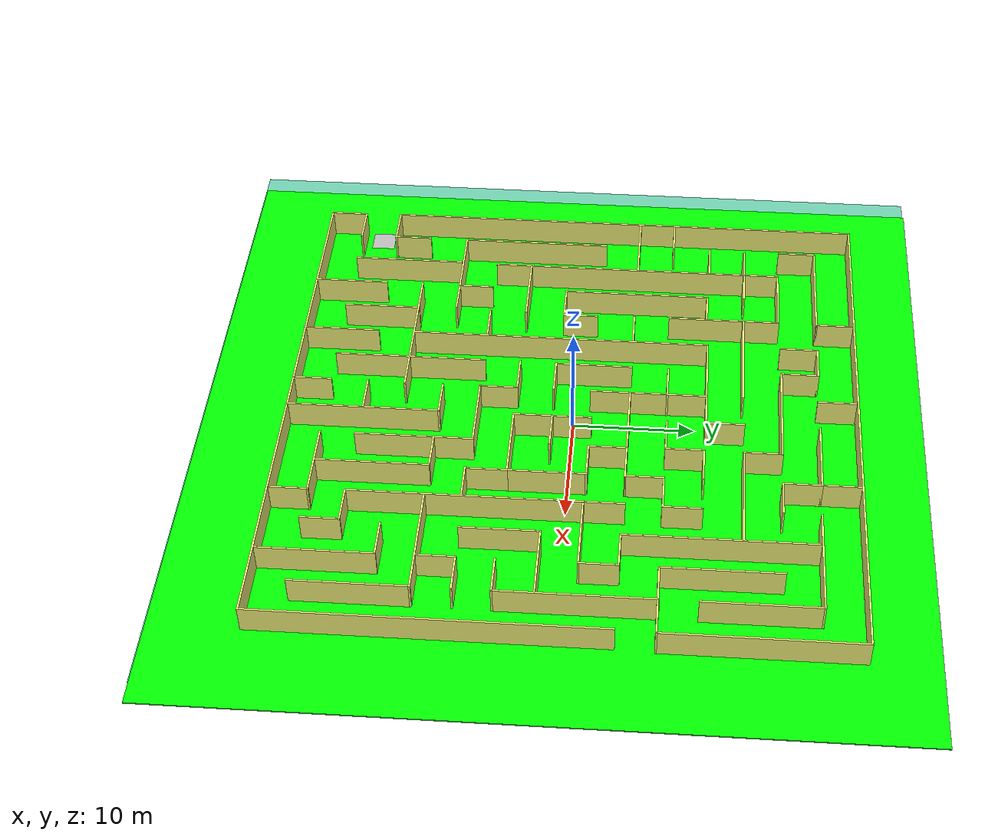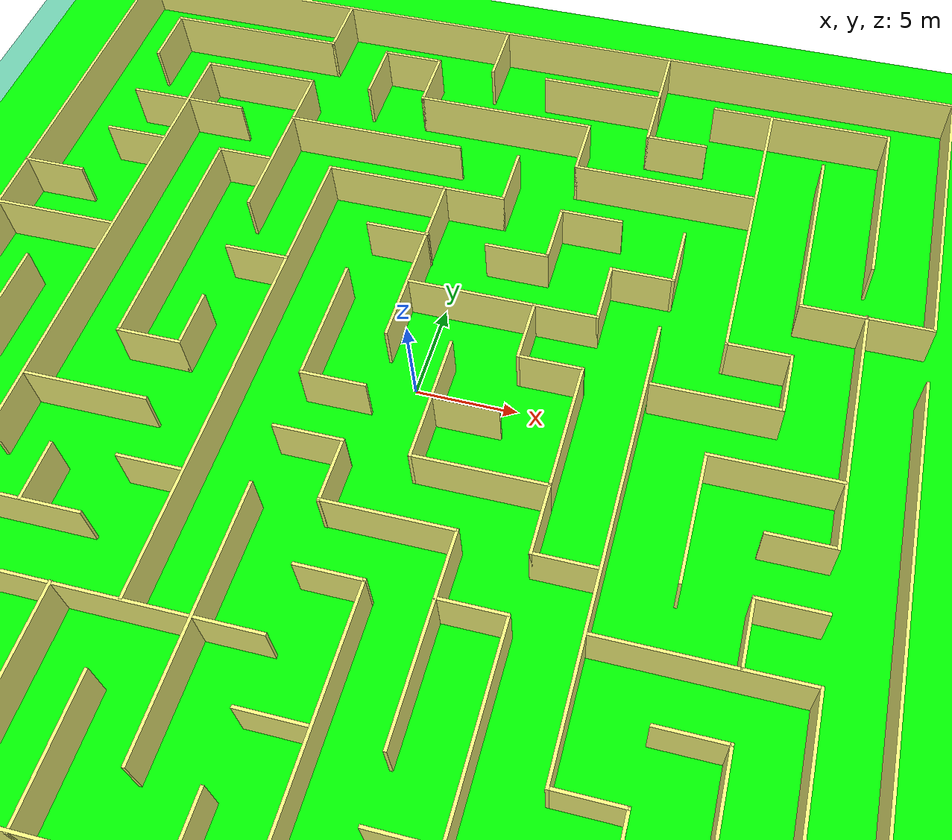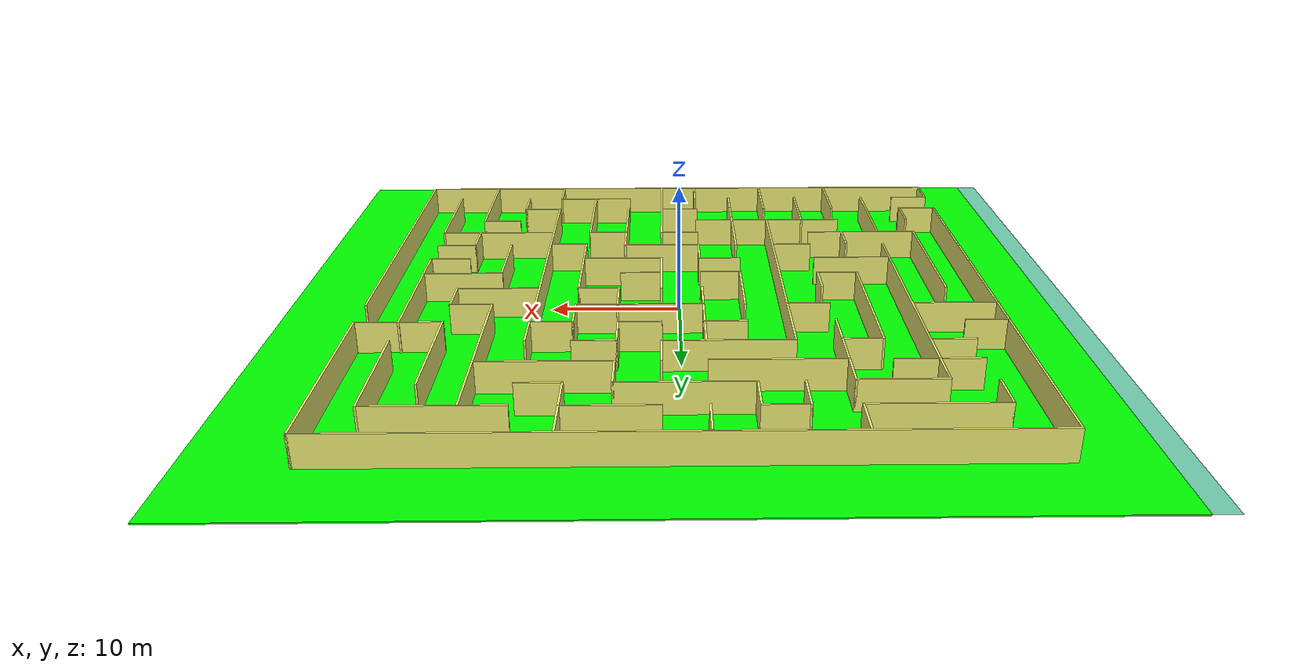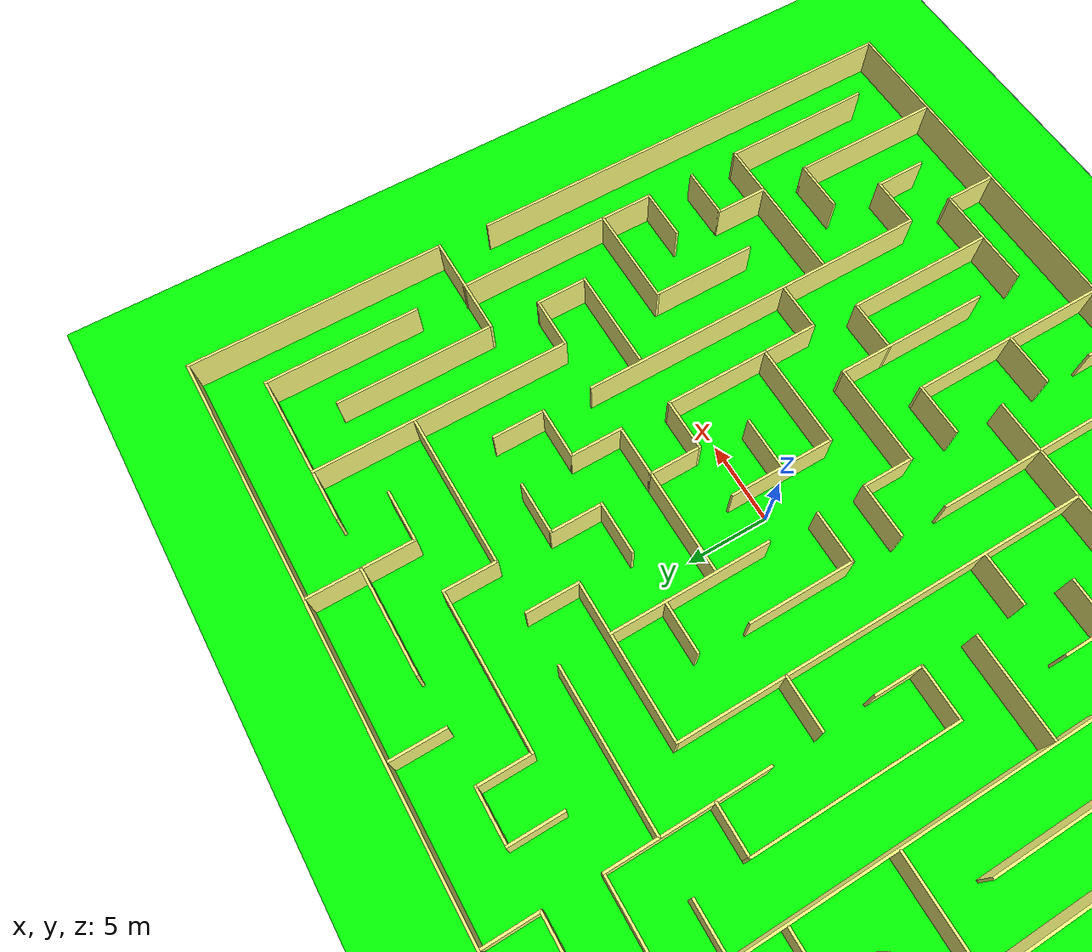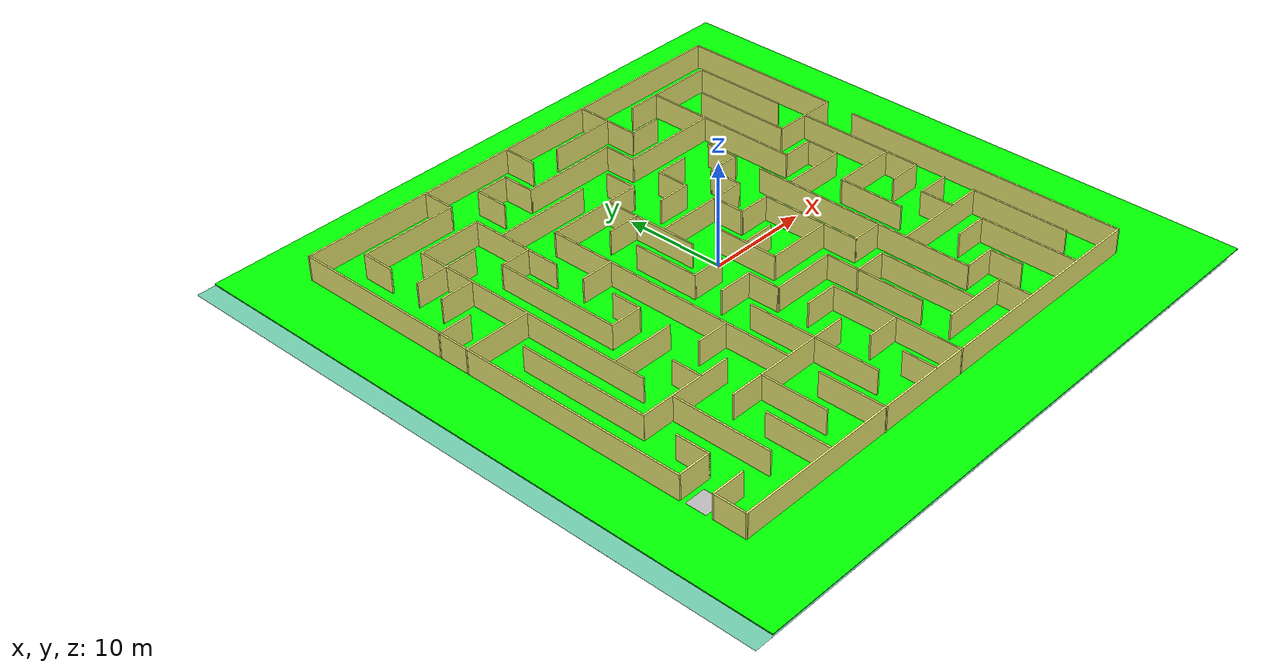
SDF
<sdf version="1.6">
 <world name="default">
  <light name="sun" type="directional">
   <pose>0 0 10 0 -0 0</pose>
   <diffuse>0.8 0.8 0.8 1</diffuse>
   <specular>0.2 0.2 0.2 1</specular>
   <attenuation>
    <range>1000</range>
    <constant>0.9</constant>
    <linear>0.01</linear>
    <quadratic>0.001</quadratic>
   </attenuation>
   <direction>-0.5 0.1 -0.9</direction>
  </light>
  <gravity>0 0 -9.8</gravity>
  <magnetic_field>6e-06 2.3e-05 -4.2e-05</magnetic_field>
  <atmosphere type="adiabatic"/>
  <physics name="default_physics" default="0" type="ode">
   <max_step_size>0.001</max_step_size>
   <real_time_factor>1</real_time_factor>
   <real_time_update_rate>1000</real_time_update_rate>
  </physics>
  <scene><ambient>0.4 0.4 0.4 1</ambient><background>0.7 0.7 0.7 1</background><shadows>1</shadows></scene>
  <audio><device>default</device></audio>
  <spherical_coordinates>
   <surface_model>EARTH_WGS84</surface_model>
   <latitude_deg>0</latitude_deg>
   <longitude_deg>0</longitude_deg>
   <elevation>0</elevation>
   <heading_deg>0</heading_deg>
  </spherical_coordinates>
  <include><uri>model://start_marker</uri><pose>-22.612965 -18.869457 0.026924 0 0 -1.57</pose></include>
  <model name="Maze3">
   <pose>-0.233521 -0.994132 0 0 -0 0</pose>
   <link name="Floor_0">
    <collision name="Floor_0_Collision">
     <geometry><box><size>60 60.01 0.1</size></box></geometry>
     <pose>0 0 0.05 0 -0 0</pose>
    </collision>
    <visual name="Floor_0_Visual">
     <pose>0 0 0.05 0 -0 0</pose>
     <geometry><box><size>60 60.01 0.1</size></box></geometry>
     <material>
      <script><uri>file://media/materials/scripts/gazebo.material</uri><name>Gazebo/Grey</name></script>
      <ambient>0 1 0 1</ambient>
     </material>
     <meta><layer>1</layer></meta>
    </visual>
    <pose>0.91648 0.050869 0.001 0 -0 0</pose>
   </link>
   <link name="Wall_0">
    <collision name="Wall_0_Collision">
     <geometry><box><size>60.01 60 0.001</size></box></geometry>
     <pose>0 0 0.0005 0 -0 0</pose>
    </collision>
    <visual name="Wall_0_Visual">
     <pose>0 0 0.0005 0 -0 0</pose>
     <geometry><box><size>60.01 60 0.001</size></box></geometry>
     <material>
      <script><uri>file://media/materials/scripts/gazebo.material</uri><name>Gazebo/Grey</name></script>
      <ambient>0.435294 0.796078 0.67451 1</ambient>
     </material>
     <meta><layer>0</layer></meta>
    </visual>
    <pose>-0.916479 -0.050868 0 0 -0 -1.5708</pose>
   </link>
   <link name="Wall_10">
    <collision name="Wall_10_Collision">
     <geometry><box><size>47.25 0.15 2.5</size></box></geometry>
     <pose>0 0 1.25 0 -0 0</pose>
    </collision>
    <visual name="Wall_10_Visual">
     <pose>0 0 1.25 0 -0 0</pose>
     <geometry><box><size>47.25 0.15 2.5</size></box></geometry>
     <material>
      <script><uri>file://media/materials/scripts/gazebo.material</uri><name>Gazebo/Grey</name></script>
      <ambient>1 1 0.5 1</ambient>
     </material>
     <meta><layer>1</layer></meta>
    </visual>
    <pose>0.135989 24.4954 0.001 0 -0 0</pose>
   </link>
   <link name="Wall_100">
    <collision name="Wall_100_Collision">
     <geometry><box><size>12.75 0.15 2.5</size></box></geometry>
     <pose>0 0 1.25 0 -0 0</pose>
    </collision>
    <visual name="Wall_100_Visual">
     <pose>0 0 1.25 0 -0 0</pose>
     <geometry><box><size>12.75 0.15 2.5</size></box></geometry>
     <material>
      <script><uri>file://media/materials/scripts/gazebo.material</uri><name>Gazebo/Grey</name></script>
      <ambient>1 1 0.5 1</ambient>
     </material>
     <meta><layer>1</layer></meta>
    </visual>
    <pose>-7.73864 -13.2116 0.001 0 -0 0</pose>
   </link>
   <link name="Wall_102">
    <collision name="Wall_102_Collision">
     <geometry><box><size>25.25 0.15 2.5</size></box></geometry>
     <pose>0 0 1.25 0 -0 0</pose>
    </collision>
    <visual name="Wall_102_Visual">
     <pose>0 0 1.25 0 -0 0</pose>
     <geometry><box><size>25.25 0.15 2.5</size></box></geometry>
     <material>
      <script><uri>file://media/materials/scripts/gazebo.material</uri><name>Gazebo/Grey</name></script>
      <ambient>1 1 0.5 1</ambient>
     </material>
     <meta><layer>1</layer></meta>
    </visual>
    <pose>-7.71415 -0.57461 0.001 0 -0 -1.5708</pose>
   </link>
   <link name="Wall_104">
    <collision name="Wall_104_Collision">
     <geometry><box><size>3.25 0.15 2.5</size></box></geometry>
     <pose>0 0 1.25 0 -0 0</pose>
    </collision>
    <visual name="Wall_104_Visual">
     <pose>0 0 1.25 0 -0 0</pose>
     <geometry><box><size>3.25 0.15 2.5</size></box></geometry>
     <material>
      <script><uri>file://media/materials/scripts/gazebo.material</uri><name>Gazebo/Grey</name></script>
      <ambient>1 1 0.5 1</ambient>
     </material>
     <meta><layer>1</layer></meta>
    </visual>
    <pose>-9.29394 5.59276 0.001 0 -0 3.14159</pose>
   </link>
   <link name="Wall_106">
    <collision name="Wall_106_Collision">
     <geometry><box><size>3.25 0.15 2.5</size></box></geometry>
     <pose>0 0 1.25 0 -0 0</pose>
    </collision>
    <visual name="Wall_106_Visual">
     <pose>0 0 1.25 0 -0 0</pose>
     <geometry><box><size>3.25 0.15 2.5</size></box></geometry>
     <material>
      <script><uri>file://media/materials/scripts/gazebo.material</uri><name>Gazebo/Grey</name></script>
      <ambient>1 1 0.5 1</ambient>
     </material>
     <meta><layer>1</layer></meta>
    </visual>
    <pose>-2.96556 8.71353 0.001 0 -0 0</pose>
   </link>
   <link name="Wall_108">
    <collision name="Wall_108_Collision">
     <geometry><box><size>9.5 0.15 2.5</size></box></geometry>
     <pose>0 0 1.25 0 -0 0</pose>
    </collision>
    <visual name="Wall_108_Visual">
     <pose>0 0 1.25 0 -0 0</pose>
     <geometry><box><size>9.5 0.15 2.5</size></box></geometry>
     <material>
      <script><uri>file://media/materials/scripts/gazebo.material</uri><name>Gazebo/Grey</name></script>
      <ambient>1 1 0.5 1</ambient>
     </material>
     <meta><layer>1</layer></meta>
    </visual>
    <pose>-3.03914 11.9754 0.001 0 -0 0</pose>
   </link>
   <link name="Wall_11">
    <collision name="Wall_11_Collision">
     <geometry><box><size>16 0.15 2.5</size></box></geometry>
     <pose>0 0 1.25 0 -0 0</pose>
    </collision>
    <visual name="Wall_11_Visual">
     <pose>0 0 1.25 0 -0 0</pose>
     <geometry><box><size>16 0.15 2.5</size></box></geometry>
     <material>
      <script><uri>file://media/materials/scripts/gazebo.material</uri><name>Gazebo/Grey</name></script>
      <ambient>1 1 0.5 1</ambient>
     </material>
     <meta><layer>1</layer></meta>
    </visual>
    <pose>23.686 16.5704 0.001 0 -0 -1.5708</pose>
   </link>
   <link name="Wall_110">
    <collision name="Wall_110_Collision">
     <geometry><box><size>6.5 0.15 2.5</size></box></geometry>
     <pose>0 0 1.25 0 -0 0</pose>
    </collision>
    <visual name="Wall_110_Visual">
     <pose>0 0 1.25 0 -0 0</pose>
     <geometry><box><size>6.5 0.15 2.5</size></box></geometry>
     <material>
      <script><uri>file://media/materials/scripts/gazebo.material</uri><name>Gazebo/Grey</name></script>
      <ambient>1 1 0.5 1</ambient>
     </material>
     <meta><layer>1</layer></meta>
    </visual>
    <pose>-10.8437 -16.3573 0.001 0 -0 -1.5708</pose>
   </link>
   <link name="Wall_112">
    <collision name="Wall_112_Collision">
     <geometry><box><size>6.5 0.15 2.5</size></box></geometry>
     <pose>0 0 1.25 0 -0 0</pose>
    </collision>
    <visual name="Wall_112_Visual">
     <pose>0 0 1.25 0 -0 0</pose>
     <geometry><box><size>6.5 0.15 2.5</size></box></geometry>
     <material>
      <script><uri>file://media/materials/scripts/gazebo.material</uri><name>Gazebo/Grey</name></script>
      <ambient>1 1 0.5 1</ambient>
     </material>
     <meta><layer>1</layer></meta>
    </visual>
    <pose>-7.70885 -19.4687 0.001 0 -0 -1.5708</pose>
   </link>
   <link name="Wall_114">
    <collision name="Wall_114_Collision">
     <geometry><box><size>12.75 0.15 2.5</size></box></geometry>
     <pose>0 0 1.25 0 -0 0</pose>
    </collision>
    <visual name="Wall_114_Visual">
     <pose>0 0 1.25 0 -0 0</pose>
     <geometry><box><size>12.75 0.15 2.5</size></box></geometry>
     <material>
      <script><uri>file://media/materials/scripts/gazebo.material</uri><name>Gazebo/Grey</name></script>
      <ambient>1 1 0.5 1</ambient>
     </material>
     <meta><layer>1</layer></meta>
    </visual>
    <pose>-4.60774 -13.1135 0.001 0 -0 -1.5708</pose>
   </link>
   <link name="Wall_116">
    <collision name="Wall_116_Collision">
     <geometry><box><size>3.41182 0.15 2.5</size></box></geometry>
     <pose>0 0 1.25 0 -0 0</pose>
    </collision>
    <visual name="Wall_116_Visual">
     <pose>0 0 1.25 0 -0 0</pose>
     <geometry><box><size>3.41182 0.15 2.5</size></box></geometry>
     <material>
      <script><uri>file://media/materials/scripts/gazebo.material</uri><name>Gazebo/Grey</name></script>
      <ambient>1 1 0.5 1</ambient>
     </material>
     <meta><layer>1</layer></meta>
    </visual>
    <pose>-3.08797 -3.79503 0.001 0 -0 0</pose>
   </link>
   <link name="Wall_118">
    <collision name="Wall_118_Collision">
     <geometry><box><size>3.25 0.15 2.5</size></box></geometry>
     <pose>0 0 1.25 0 -0 0</pose>
    </collision>
    <visual name="Wall_118_Visual">
     <pose>0 0 1.25 0 -0 0</pose>
     <geometry><box><size>3.25 0.15 2.5</size></box></geometry>
     <material>
      <script><uri>file://media/materials/scripts/gazebo.material</uri><name>Gazebo/Grey</name></script>
      <ambient>1 1 0.5 1</ambient>
     </material>
     <meta><layer>1</layer></meta>
    </visual>
    <pose>-1.45706 -5.36526 0.001 0 -0 -1.5708</pose>
   </link>
   <link name="Wall_119">
    <collision name="Wall_119_Collision">
     <geometry><box><size>6.33818 0.15 2.5</size></box></geometry>
     <pose>0 0 1.25 0 -0 0</pose>
    </collision>
    <visual name="Wall_119_Visual">
     <pose>0 0 1.25 0 -0 0</pose>
     <geometry><box><size>6.33818 0.15 2.5</size></box></geometry>
     <material>
      <script><uri>file://media/materials/scripts/gazebo.material</uri><name>Gazebo/Grey</name></script>
      <ambient>1 1 0.5 1</ambient>
     </material>
     <meta><layer>1</layer></meta>
    </visual>
    <pose>1.63703 -6.89503 0.001 0 -0 0</pose>
   </link>
   <link name="Wall_12">
    <collision name="Wall_12_Collision">
     <geometry><box><size>6.5 0.15 2.5</size></box></geometry>
     <pose>0 0 1.25 0 -0 0</pose>
    </collision>
    <visual name="Wall_12_Visual">
     <pose>0 0 1.25 0 -0 0</pose>
     <geometry><box><size>6.5 0.15 2.5</size></box></geometry>
     <material>
      <script><uri>file://media/materials/scripts/gazebo.material</uri><name>Gazebo/Grey</name></script>
      <ambient>1 1 0.5 1</ambient>
     </material>
     <meta><layer>1</layer></meta>
    </visual>
    <pose>20.511 8.64537 0.001 0 -0 3.14159</pose>
   </link>
   <link name="Wall_120">
    <collision name="Wall_120_Collision">
     <geometry><box><size>9.75 0.15 2.5</size></box></geometry>
     <pose>0 0 1.25 0 -0 0</pose>
    </collision>
    <visual name="Wall_120_Visual">
     <pose>0 0 1.25 0 -0 0</pose>
     <geometry><box><size>9.75 0.15 2.5</size></box></geometry>
     <material>
      <script><uri>file://media/materials/scripts/gazebo.material</uri><name>Gazebo/Grey</name></script>
      <ambient>1 1 0.5 1</ambient>
     </material>
     <meta><layer>1</layer></meta>
    </visual>
    <pose>4.73112 -11.695 0.001 0 -0 -1.5708</pose>
   </link>
   <link name="Wall_13">
    <collision name="Wall_13_Collision">
     <geometry><box><size>9.75 0.15 2.5</size></box></geometry>
     <pose>0 0 1.25 0 -0 0</pose>
    </collision>
    <visual name="Wall_13_Visual">
     <pose>0 0 1.25 0 -0 0</pose>
     <geometry><box><size>9.75 0.15 2.5</size></box></geometry>
     <material>
      <script><uri>file://media/materials/scripts/gazebo.material</uri><name>Gazebo/Grey</name></script>
      <ambient>1 1 0.5 1</ambient>
     </material>
     <meta><layer>1</layer></meta>
    </visual>
    <pose>17.336 13.4454 0.001 0 -0 1.5708</pose>
   </link>
   <link name="Wall_131">
    <collision name="Wall_131_Collision">
     <geometry><box><size>12.75 0.15 2.5</size></box></geometry>
     <pose>0 0 1.25 0 -0 0</pose>
    </collision>
    <visual name="Wall_131_Visual">
     <pose>0 0 1.25 0 -0 0</pose>
     <geometry><box><size>12.75 0.15 2.5</size></box></geometry>
     <material>
      <script><uri>file://media/materials/scripts/gazebo.material</uri><name>Gazebo/Grey</name></script>
      <ambient>1 1 0.5 1</ambient>
     </material>
     <meta><layer>1</layer></meta>
    </visual>
    <pose>1.6821 -16.3109 0.001 0 -0 1.5708</pose>
   </link>
   <link name="Wall_132">
    <collision name="Wall_132_Collision">
     <geometry><box><size>3.25 0.15 2.5</size></box></geometry>
     <pose>0 0 1.25 0 -0 0</pose>
    </collision>
    <visual name="Wall_132_Visual">
     <pose>0 0 1.25 0 -0 0</pose>
     <geometry><box><size>3.25 0.15 2.5</size></box></geometry>
     <material>
      <script><uri>file://media/materials/scripts/gazebo.material</uri><name>Gazebo/Grey</name></script>
      <ambient>1 1 0.5 1</ambient>
     </material>
     <meta><layer>1</layer></meta>
    </visual>
    <pose>0.132105 -10.0109 0.001 0 -0 3.14159</pose>
   </link>
   <link name="Wall_134">
    <collision name="Wall_134_Collision">
     <geometry><box><size>3.25 0.15 2.5</size></box></geometry>
     <pose>0 0 1.25 0 -0 0</pose>
    </collision>
    <visual name="Wall_134_Visual">
     <pose>0 0 1.25 0 -0 0</pose>
     <geometry><box><size>3.25 0.15 2.5</size></box></geometry>
     <material>
      <script><uri>file://media/materials/scripts/gazebo.material</uri><name>Gazebo/Grey</name></script>
      <ambient>1 1 0.5 1</ambient>
     </material>
     <meta><layer>1</layer></meta>
    </visual>
    <pose>0.039057 -16.3069 0.001 0 -0 3.14159</pose>
   </link>
   <link name="Wall_136">
    <collision name="Wall_136_Collision">
     <geometry><box><size>3.25 0.15 2.5</size></box></geometry>
     <pose>0 0 1.25 0 -0 0</pose>
    </collision>
    <visual name="Wall_136_Visual">
     <pose>0 0 1.25 0 -0 0</pose>
     <geometry><box><size>3.25 0.15 2.5</size></box></geometry>
     <material>
      <script><uri>file://media/materials/scripts/gazebo.material</uri><name>Gazebo/Grey</name></script>
      <ambient>1 1 0.5 1</ambient>
     </material>
     <meta><layer>1</layer></meta>
    </visual>
    <pose>-1.45826 -20.9911 0.001 0 -0 1.5708</pose>
   </link>
   <link name="Wall_138">
    <collision name="Wall_138_Collision">
     <geometry><box><size>9.75 0.15 2.5</size></box></geometry>
     <pose>0 0 1.25 0 -0 0</pose>
    </collision>
    <visual name="Wall_138_Visual">
     <pose>0 0 1.25 0 -0 0</pose>
     <geometry><box><size>9.75 0.15 2.5</size></box></geometry>
     <material>
      <script><uri>file://media/materials/scripts/gazebo.material</uri><name>Gazebo/Grey</name></script>
      <ambient>1 1 0.5 1</ambient>
     </material>
     <meta><layer>1</layer></meta>
    </visual>
    <pose>-1.47426 7.16575 0.001 0 -0 -1.5708</pose>
   </link>
   <link name="Wall_140">
    <collision name="Wall_140_Collision">
     <geometry><box><size>6.5 0.15 2.5</size></box></geometry>
     <pose>0 0 1.25 0 -0 0</pose>
    </collision>
    <visual name="Wall_140_Visual">
     <pose>0 0 1.25 0 -0 0</pose>
     <geometry><box><size>6.5 0.15 2.5</size></box></geometry>
     <material>
      <script><uri>file://media/materials/scripts/gazebo.material</uri><name>Gazebo/Grey</name></script>
      <ambient>1 1 0.5 1</ambient>
     </material>
     <meta><layer>1</layer></meta>
    </visual>
    <pose>-4.58142 2.42261 0.001 0 -0 -1.5708</pose>
   </link>
   <link name="Wall_141">
    <collision name="Wall_141_Collision">
     <geometry><box><size>3.25 0.15 2.5</size></box></geometry>
     <pose>0 0 1.25 0 -0 0</pose>
    </collision>
    <visual name="Wall_141_Visual">
     <pose>0 0 1.25 0 -0 0</pose>
     <geometry><box><size>3.25 0.15 2.5</size></box></geometry>
     <material>
      <script><uri>file://media/materials/scripts/gazebo.material</uri><name>Gazebo/Grey</name></script>
      <ambient>1 1 0.5 1</ambient>
     </material>
     <meta><layer>1</layer></meta>
    </visual>
    <pose>-3.03142 -0.75239 0.001 0 -0 0</pose>
   </link>
   <link name="Wall_143">
    <collision name="Wall_143_Collision">
     <geometry><box><size>6.5 0.15 2.5</size></box></geometry>
     <pose>0 0 1.25 0 -0 0</pose>
    </collision>
    <visual name="Wall_143_Visual">
     <pose>0 0 1.25 0 -0 0</pose>
     <geometry><box><size>6.5 0.15 2.5</size></box></geometry>
     <material>
      <script><uri>file://media/materials/scripts/gazebo.material</uri><name>Gazebo/Grey</name></script>
      <ambient>1 1 0.5 1</ambient>
     </material>
     <meta><layer>1</layer></meta>
    </visual>
    <pose>1.66366 -0.653784 0.001 0 -0 -1.5708</pose>
   </link>
   <link name="Wall_144">
    <collision name="Wall_144_Collision">
     <geometry><box><size>6.5 0.15 2.5</size></box></geometry>
     <pose>0 0 1.25 0 -0 0</pose>
    </collision>
    <visual name="Wall_144_Visual">
     <pose>0 0 1.25 0 -0 0</pose>
     <geometry><box><size>6.5 0.15 2.5</size></box></geometry>
     <material>
      <script><uri>file://media/materials/scripts/gazebo.material</uri><name>Gazebo/Grey</name></script>
      <ambient>1 1 0.5 1</ambient>
     </material>
     <meta><layer>1</layer></meta>
    </visual>
    <pose>4.83866 -3.82878 0.001 0 -0 0</pose>
   </link>
   <link name="Wall_145">
    <collision name="Wall_145_Collision">
     <geometry><box><size>6.5 0.15 2.5</size></box></geometry>
     <pose>0 0 1.25 0 -0 0</pose>
    </collision>
    <visual name="Wall_145_Visual">
     <pose>0 0 1.25 0 -0 0</pose>
     <geometry><box><size>6.5 0.15 2.5</size></box></geometry>
     <material>
      <script><uri>file://media/materials/scripts/gazebo.material</uri><name>Gazebo/Grey</name></script>
      <ambient>1 1 0.5 1</ambient>
     </material>
     <meta><layer>1</layer></meta>
    </visual>
    <pose>8.01366 -0.653784 0.001 0 -0 1.5708</pose>
   </link>
   <link name="Wall_146">
    <collision name="Wall_146_Collision">
     <geometry><box><size>3.25 0.15 2.5</size></box></geometry>
     <pose>0 0 1.25 0 -0 0</pose>
    </collision>
    <visual name="Wall_146_Visual">
     <pose>0 0 1.25 0 -0 0</pose>
     <geometry><box><size>3.25 0.15 2.5</size></box></geometry>
     <material>
      <script><uri>file://media/materials/scripts/gazebo.material</uri><name>Gazebo/Grey</name></script>
      <ambient>1 1 0.5 1</ambient>
     </material>
     <meta><layer>1</layer></meta>
    </visual>
    <pose>6.46366 2.52122 0.001 0 -0 3.14159</pose>
   </link>
   <link name="Wall_147">
    <collision name="Wall_147_Collision">
     <geometry><box><size>3.25 0.15 2.5</size></box></geometry>
     <pose>0 0 1.25 0 -0 0</pose>
    </collision>
    <visual name="Wall_147_Visual">
     <pose>0 0 1.25 0 -0 0</pose>
     <geometry><box><size>3.25 0.15 2.5</size></box></geometry>
     <material>
      <script><uri>file://media/materials/scripts/gazebo.material</uri><name>Gazebo/Grey</name></script>
      <ambient>1 1 0.5 1</ambient>
     </material>
     <meta><layer>1</layer></meta>
    </visual>
    <pose>4.91366 4.07122 0.001 0 -0 1.5708</pose>
   </link>
   <link name="Wall_148">
    <collision name="Wall_148_Collision">
     <geometry><box><size>6.5 0.15 2.5</size></box></geometry>
     <pose>0 0 1.25 0 -0 0</pose>
    </collision>
    <visual name="Wall_148_Visual">
     <pose>0 0 1.25 0 -0 0</pose>
     <geometry><box><size>6.5 0.15 2.5</size></box></geometry>
     <material>
      <script><uri>file://media/materials/scripts/gazebo.material</uri><name>Gazebo/Grey</name></script>
      <ambient>1 1 0.5 1</ambient>
     </material>
     <meta><layer>1</layer></meta>
    </visual>
    <pose>1.73866 5.62122 0.001 0 -0 3.14159</pose>
   </link>
   <link name="Wall_15">
    <collision name="Wall_15_Collision">
     <geometry><box><size>9.5 0.15 2.5</size></box></geometry>
     <pose>0 0 1.25 0 -0 0</pose>
    </collision>
    <visual name="Wall_15_Visual">
     <pose>0 0 1.25 0 -0 0</pose>
     <geometry><box><size>9.5 0.15 2.5</size></box></geometry>
     <material>
      <script><uri>file://media/materials/scripts/gazebo.material</uri><name>Gazebo/Grey</name></script>
      <ambient>1 1 0.5 1</ambient>
     </material>
     <meta><layer>1</layer></meta>
    </visual>
    <pose>20.4894 16.4908 0.001 0 -0 1.5708</pose>
   </link>
   <link name="Wall_150">
    <collision name="Wall_150_Collision">
     <geometry><box><size>3.25 0.15 2.5</size></box></geometry>
     <pose>0 0 1.25 0 -0 0</pose>
    </collision>
    <visual name="Wall_150_Visual">
     <pose>0 0 1.25 0 -0 0</pose>
     <geometry><box><size>3.25 0.15 2.5</size></box></geometry>
     <material>
      <script><uri>file://media/materials/scripts/gazebo.material</uri><name>Gazebo/Grey</name></script>
      <ambient>1 1 0.5 1</ambient>
     </material>
     <meta><layer>1</layer></meta>
    </visual>
    <pose>6.46366 5.62122 0.001 0 -0 0</pose>
   </link>
   <link name="Wall_151">
    <collision name="Wall_151_Collision">
     <geometry><box><size>3.25 0.15 2.5</size></box></geometry>
     <pose>0 0 1.25 0 -0 0</pose>
    </collision>
    <visual name="Wall_151_Visual">
     <pose>0 0 1.25 0 -0 0</pose>
     <geometry><box><size>3.25 0.15 2.5</size></box></geometry>
     <material>
      <script><uri>file://media/materials/scripts/gazebo.material</uri><name>Gazebo/Grey</name></script>
      <ambient>1 1 0.5 1</ambient>
     </material>
     <meta><layer>1</layer></meta>
    </visual>
    <pose>8.01366 7.17122 0.001 0 -0 1.5708</pose>
   </link>
   <link name="Wall_152">
    <collision name="Wall_152_Collision">
     <geometry><box><size>3.25 0.15 2.5</size></box></geometry>
     <pose>0 0 1.25 0 -0 0</pose>
    </collision>
    <visual name="Wall_152_Visual">
     <pose>0 0 1.25 0 -0 0</pose>
     <geometry><box><size>3.25 0.15 2.5</size></box></geometry>
     <material>
      <script><uri>file://media/materials/scripts/gazebo.material</uri><name>Gazebo/Grey</name></script>
      <ambient>1 1 0.5 1</ambient>
     </material>
     <meta><layer>1</layer></meta>
    </visual>
    <pose>9.56366 8.72122 0.001 0 -0 0</pose>
   </link>
   <link name="Wall_153">
    <collision name="Wall_153_Collision">
     <geometry><box><size>3.25 0.15 2.5</size></box></geometry>
     <pose>0 0 1.25 0 -0 0</pose>
    </collision>
    <visual name="Wall_153_Visual">
     <pose>0 0 1.25 0 -0 0</pose>
     <geometry><box><size>3.25 0.15 2.5</size></box></geometry>
     <material>
      <script><uri>file://media/materials/scripts/gazebo.material</uri><name>Gazebo/Grey</name></script>
      <ambient>1 1 0.5 1</ambient>
     </material>
     <meta><layer>1</layer></meta>
    </visual>
    <pose>11.1137 10.2712 0.001 0 -0 1.5708</pose>
   </link>
   <link name="Wall_157">
    <collision name="Wall_157_Collision">
     <geometry><box><size>3.25 0.15 2.5</size></box></geometry>
     <pose>0 0 1.25 0 -0 0</pose>
    </collision>
    <visual name="Wall_157_Visual">
     <pose>0 0 1.25 0 -0 0</pose>
     <geometry><box><size>3.25 0.15 2.5</size></box></geometry>
     <material>
      <script><uri>file://media/materials/scripts/gazebo.material</uri><name>Gazebo/Grey</name></script>
      <ambient>1 1 0.5 1</ambient>
     </material>
     <meta><layer>1</layer></meta>
    </visual>
    <pose>3.21366 8.76629 0.001 0 -0 0</pose>
   </link>
   <link name="Wall_158">
    <collision name="Wall_158_Collision">
     <geometry><box><size>3.25 0.15 2.5</size></box></geometry>
     <pose>0 0 1.25 0 -0 0</pose>
    </collision>
    <visual name="Wall_158_Visual">
     <pose>0 0 1.25 0 -0 0</pose>
     <geometry><box><size>3.25 0.15 2.5</size></box></geometry>
     <material>
      <script><uri>file://media/materials/scripts/gazebo.material</uri><name>Gazebo/Grey</name></script>
      <ambient>1 1 0.5 1</ambient>
     </material>
     <meta><layer>1</layer></meta>
    </visual>
    <pose>4.76366 10.3163 0.001 0 -0 1.5708</pose>
   </link>
   <link name="Wall_159">
    <collision name="Wall_159_Collision">
     <geometry><box><size>3.25 0.15 2.5</size></box></geometry>
     <pose>0 0 1.25 0 -0 0</pose>
    </collision>
    <visual name="Wall_159_Visual">
     <pose>0 0 1.25 0 -0 0</pose>
     <geometry><box><size>3.25 0.15 2.5</size></box></geometry>
     <material>
      <script><uri>file://media/materials/scripts/gazebo.material</uri><name>Gazebo/Grey</name></script>
      <ambient>1 1 0.5 1</ambient>
     </material>
     <meta><layer>1</layer></meta>
    </visual>
    <pose>6.31366 11.8663 0.001 0 -0 0</pose>
   </link>
   <link name="Wall_16">
    <collision name="Wall_16_Collision">
     <geometry><box><size>9.5 0.15 2.5</size></box></geometry>
     <pose>0 0 1.25 0 -0 0</pose>
    </collision>
    <visual name="Wall_16_Visual">
     <pose>0 0 1.25 0 -0 0</pose>
     <geometry><box><size>9.5 0.15 2.5</size></box></geometry>
     <material>
      <script><uri>file://media/materials/scripts/gazebo.material</uri><name>Gazebo/Grey</name></script>
      <ambient>1 1 0.5 1</ambient>
     </material>
     <meta><layer>1</layer></meta>
    </visual>
    <pose>15.8144 21.1658 0.001 0 -0 3.14159</pose>
   </link>
   <link name="Wall_161">
    <collision name="Wall_161_Collision">
     <geometry><box><size>3.25 0.15 2.5</size></box></geometry>
     <pose>0 0 1.25 0 -0 0</pose>
    </collision>
    <visual name="Wall_161_Visual">
     <pose>0 0 1.25 0 -0 0</pose>
     <geometry><box><size>3.25 0.15 2.5</size></box></geometry>
     <material>
      <script><uri>file://media/materials/scripts/gazebo.material</uri><name>Gazebo/Grey</name></script>
      <ambient>1 1 0.5 1</ambient>
     </material>
     <meta><layer>1</layer></meta>
    </visual>
    <pose>1.63586 13.5254 0.001 0 -0 1.5708</pose>
   </link>
   <link name="Wall_163">
    <collision name="Wall_163_Collision">
     <geometry><box><size>9.5 0.15 2.5</size></box></geometry>
     <pose>0 0 1.25 0 -0 0</pose>
    </collision>
    <visual name="Wall_163_Visual">
     <pose>0 0 1.25 0 -0 0</pose>
     <geometry><box><size>9.5 0.15 2.5</size></box></geometry>
     <material>
      <script><uri>file://media/materials/scripts/gazebo.material</uri><name>Gazebo/Grey</name></script>
      <ambient>1 1 0.5 1</ambient>
     </material>
     <meta><layer>1</layer></meta>
    </visual>
    <pose>-6.24665 14.9929 0.001 0 -0 0</pose>
   </link>
   <link name="Wall_165">
    <collision name="Wall_165_Collision">
     <geometry><box><size>3.25 0.15 2.5</size></box></geometry>
     <pose>0 0 1.25 0 -0 0</pose>
    </collision>
    <visual name="Wall_165_Visual">
     <pose>0 0 1.25 0 -0 0</pose>
     <geometry><box><size>3.25 0.15 2.5</size></box></geometry>
     <material>
      <script><uri>file://media/materials/scripts/gazebo.material</uri><name>Gazebo/Grey</name></script>
      <ambient>1 1 0.5 1</ambient>
     </material>
     <meta><layer>1</layer></meta>
    </visual>
    <pose>3.2864 -0.644379 0.001 0 -0 0</pose>
   </link>
   <link name="Wall_167">
    <collision name="Wall_167_Collision">
     <geometry><box><size>3.5 0.15 2.5</size></box></geometry>
     <pose>0 0 1.25 0 -0 0</pose>
    </collision>
    <visual name="Wall_167_Visual">
     <pose>0 0 1.25 0 -0 0</pose>
     <geometry><box><size>3.5 0.15 2.5</size></box></geometry>
     <material>
      <script><uri>file://media/materials/scripts/gazebo.material</uri><name>Gazebo/Grey</name></script>
      <ambient>1 1 0.5 1</ambient>
     </material>
     <meta><layer>1</layer></meta>
    </visual>
    <pose>8.01366 -5.50378 0.001 0 -0 -1.5708</pose>
   </link>
   <link name="Wall_168">
    <collision name="Wall_168_Collision">
     <geometry><box><size>3 0.15 2.5</size></box></geometry>
     <pose>0 0 1.25 0 -0 0</pose>
    </collision>
    <visual name="Wall_168_Visual">
     <pose>0 0 1.25 0 -0 0</pose>
     <geometry><box><size>3 0.15 2.5</size></box></geometry>
     <material>
      <script><uri>file://media/materials/scripts/gazebo.material</uri><name>Gazebo/Grey</name></script>
      <ambient>1 1 0.5 1</ambient>
     </material>
     <meta><layer>1</layer></meta>
    </visual>
    <pose>9.43866 -7.17878 0.001 0 -0 0</pose>
   </link>
   <link name="Wall_170">
    <collision name="Wall_170_Collision">
     <geometry><box><size>3.25 0.15 2.5</size></box></geometry>
     <pose>0 0 1.25 0 -0 0</pose>
    </collision>
    <visual name="Wall_170_Visual">
     <pose>0 0 1.25 0 -0 0</pose>
     <geometry><box><size>3.25 0.15 2.5</size></box></geometry>
     <material>
      <script><uri>file://media/materials/scripts/gazebo.material</uri><name>Gazebo/Grey</name></script>
      <ambient>1 1 0.5 1</ambient>
     </material>
     <meta><layer>1</layer></meta>
    </visual>
    <pose>6.27338 -10.0795 0.001 0 -0 0</pose>
   </link>
   <link name="Wall_172">
    <collision name="Wall_172_Collision">
     <geometry><box><size>9.25 0.15 2.5</size></box></geometry>
     <pose>0 0 1.25 0 -0 0</pose>
    </collision>
    <visual name="Wall_172_Visual">
     <pose>0 0 1.25 0 -0 0</pose>
     <geometry><box><size>9.25 0.15 2.5</size></box></geometry>
     <material>
      <script><uri>file://media/materials/scripts/gazebo.material</uri><name>Gazebo/Grey</name></script>
      <ambient>1 1 0.5 1</ambient>
     </material>
     <meta><layer>1</layer></meta>
    </visual>
    <pose>7.85976 -14.6816 0.001 0 -0 1.5708</pose>
   </link>
   <link name="Wall_175">
    <collision name="Wall_175_Collision">
     <geometry><box><size>3.25 0.15 2.5</size></box></geometry>
     <pose>0 0 1.25 0 -0 0</pose>
    </collision>
    <visual name="Wall_175_Visual">
     <pose>0 0 1.25 0 -0 0</pose>
     <geometry><box><size>3.25 0.15 2.5</size></box></geometry>
     <material>
      <script><uri>file://media/materials/scripts/gazebo.material</uri><name>Gazebo/Grey</name></script>
      <ambient>1 1 0.5 1</ambient>
     </material>
     <meta><layer>1</layer></meta>
    </visual>
    <pose>-1.42323 22.7551 0.001 0 -0 1.5708</pose>
   </link>
   <link name="Wall_177">
    <collision name="Wall_177_Collision">
     <geometry><box><size>6.5 0.15 2.5</size></box></geometry>
     <pose>0 0 1.25 0 -0 0</pose>
    </collision>
    <visual name="Wall_177_Visual">
     <pose>0 0 1.25 0 -0 0</pose>
     <geometry><box><size>6.5 0.15 2.5</size></box></geometry>
     <material>
      <script><uri>file://media/materials/scripts/gazebo.material</uri><name>Gazebo/Grey</name></script>
      <ambient>1 1 0.5 1</ambient>
     </material>
     <meta><layer>1</layer></meta>
    </visual>
    <pose>4.81226 21.2679 0.001 0 -0 0</pose>
   </link>
   <link name="Wall_178">
    <collision name="Wall_178_Collision">
     <geometry><box><size>3.25 0.15 2.5</size></box></geometry>
     <pose>0 0 1.25 0 -0 0</pose>
    </collision>
    <visual name="Wall_178_Visual">
     <pose>0 0 1.25 0 -0 0</pose>
     <geometry><box><size>3.25 0.15 2.5</size></box></geometry>
     <material>
      <script><uri>file://media/materials/scripts/gazebo.material</uri><name>Gazebo/Grey</name></script>
      <ambient>1 1 0.5 1</ambient>
     </material>
     <meta><layer>1</layer></meta>
    </visual>
    <pose>7.98726 22.8179 0.001 0 -0 1.5708</pose>
   </link>
   <link name="Wall_18">
    <collision name="Wall_18_Collision">
     <geometry><box><size>15.75 0.15 2.5</size></box></geometry>
     <pose>0 0 1.25 0 -0 0</pose>
    </collision>
    <visual name="Wall_18_Visual">
     <pose>0 0 1.25 0 -0 0</pose>
     <geometry><box><size>15.75 0.15 2.5</size></box></geometry>
     <material>
      <script><uri>file://media/materials/scripts/gazebo.material</uri><name>Gazebo/Grey</name></script>
      <ambient>1 1 0.5 1</ambient>
     </material>
     <meta><layer>1</layer></meta>
    </visual>
    <pose>14.2274 13.3557 0.001 0 -0 -1.5708</pose>
   </link>
   <link name="Wall_180">
    <collision name="Wall_180_Collision">
     <geometry><box><size>3.25 0.15 2.5</size></box></geometry>
     <pose>0 0 1.25 0 -0 0</pose>
    </collision>
    <visual name="Wall_180_Visual">
     <pose>0 0 1.25 0 -0 0</pose>
     <geometry><box><size>3.25 0.15 2.5</size></box></geometry>
     <material>
      <script><uri>file://media/materials/scripts/gazebo.material</uri><name>Gazebo/Grey</name></script>
      <ambient>1 1 0.5 1</ambient>
     </material>
     <meta><layer>1</layer></meta>
    </visual>
    <pose>7.98726 19.7179 0.001 0 -0 -1.5708</pose>
   </link>
   <link name="Wall_181">
    <collision name="Wall_181_Collision">
     <geometry><box><size>3.25 0.15 2.5</size></box></geometry>
     <pose>0 0 1.25 0 -0 0</pose>
    </collision>
    <visual name="Wall_181_Visual">
     <pose>0 0 1.25 0 -0 0</pose>
     <geometry><box><size>3.25 0.15 2.5</size></box></geometry>
     <material>
      <script><uri>file://media/materials/scripts/gazebo.material</uri><name>Gazebo/Grey</name></script>
      <ambient>1 1 0.5 1</ambient>
     </material>
     <meta><layer>1</layer></meta>
    </visual>
    <pose>9.53726 18.1679 0.001 0 -0 0</pose>
   </link>
   <link name="Wall_19">
    <collision name="Wall_19_Collision">
     <geometry><box><size>3.25 0.15 2.5</size></box></geometry>
     <pose>0 0 1.25 0 -0 0</pose>
    </collision>
    <visual name="Wall_19_Visual">
     <pose>0 0 1.25 0 -0 0</pose>
     <geometry><box><size>3.25 0.15 2.5</size></box></geometry>
     <material>
      <script><uri>file://media/materials/scripts/gazebo.material</uri><name>Gazebo/Grey</name></script>
      <ambient>1 1 0.5 1</ambient>
     </material>
     <meta><layer>1</layer></meta>
    </visual>
    <pose>15.7774 5.55574 0.001 0 -0 0</pose>
   </link>
   <link name="Wall_2">
    <collision name="Wall_2_Collision">
     <geometry><box><size>60.01 60 0.001</size></box></geometry>
     <pose>0 0 0.0005 0 -0 0</pose>
    </collision>
    <visual name="Wall_2_Visual">
     <pose>0 0 0.0005 0 -0 0</pose>
     <geometry><box><size>60.01 60 0.001</size></box></geometry>
     <material>
      <script><uri>file://media/materials/scripts/gazebo.material</uri><name>Gazebo/Grey</name></script>
      <ambient>1 1 0.5 1</ambient>
     </material>
     <meta><layer>1</layer></meta>
    </visual>
    <pose>0.91648 0.050869 0.001 0 -0 -1.5708</pose>
   </link>
   <link name="Wall_20">
    <collision name="Wall_20_Collision">
     <geometry><box><size>3.25 0.15 2.5</size></box></geometry>
     <pose>0 0 1.25 0 -0 0</pose>
    </collision>
    <visual name="Wall_20_Visual">
     <pose>0 0 1.25 0 -0 0</pose>
     <geometry><box><size>3.25 0.15 2.5</size></box></geometry>
     <material>
      <script><uri>file://media/materials/scripts/gazebo.material</uri><name>Gazebo/Grey</name></script>
      <ambient>1 1 0.5 1</ambient>
     </material>
     <meta><layer>1</layer></meta>
    </visual>
    <pose>17.3274 4.00574 0.001 0 -0 -1.5708</pose>
   </link>
   <link name="Wall_21">
    <collision name="Wall_21_Collision">
     <geometry><box><size>6.25 0.15 2.5</size></box></geometry>
     <pose>0 0 1.25 0 -0 0</pose>
    </collision>
    <visual name="Wall_21_Visual">
     <pose>0 0 1.25 0 -0 0</pose>
     <geometry><box><size>6.25 0.15 2.5</size></box></geometry>
     <material>
      <script><uri>file://media/materials/scripts/gazebo.material</uri><name>Gazebo/Grey</name></script>
      <ambient>1 1 0.5 1</ambient>
     </material>
     <meta><layer>1</layer></meta>
    </visual>
    <pose>14.2774 2.45574 0.001 0 -0 3.14159</pose>
   </link>
   <link name="Wall_23">
    <collision name="Wall_23_Collision">
     <geometry><box><size>12.75 0.15 2.5</size></box></geometry>
     <pose>0 0 1.25 0 -0 0</pose>
    </collision>
    <visual name="Wall_23_Visual">
     <pose>0 0 1.25 0 -0 0</pose>
     <geometry><box><size>12.75 0.15 2.5</size></box></geometry>
     <material>
      <script><uri>file://media/materials/scripts/gazebo.material</uri><name>Gazebo/Grey</name></script>
      <ambient>1 1 0.5 1</ambient>
     </material>
     <meta><layer>1</layer></meta>
    </visual>
    <pose>20.4935 2.3978 0.001 0 -0 -1.5708</pose>
   </link>
   <link name="Wall_24">
    <collision name="Wall_24_Collision">
     <geometry><box><size>3.25 0.15 2.5</size></box></geometry>
     <pose>0 0 1.25 0 -0 0</pose>
    </collision>
    <visual name="Wall_24_Visual">
     <pose>0 0 1.25 0 -0 0</pose>
     <geometry><box><size>3.25 0.15 2.5</size></box></geometry>
     <material>
      <script><uri>file://media/materials/scripts/gazebo.material</uri><name>Gazebo/Grey</name></script>
      <ambient>1 1 0.5 1</ambient>
     </material>
     <meta><layer>1</layer></meta>
    </visual>
    <pose>18.9435 -3.9022 0.001 0 -0 3.14159</pose>
   </link>
   <link name="Wall_27">
    <collision name="Wall_27_Collision">
     <geometry><box><size>6.25 0.15 2.5</size></box></geometry>
     <pose>0 0 1.25 0 -0 0</pose>
    </collision>
    <visual name="Wall_27_Visual">
     <pose>0 0 1.25 0 -0 0</pose>
     <geometry><box><size>6.25 0.15 2.5</size></box></geometry>
     <material>
      <script><uri>file://media/materials/scripts/gazebo.material</uri><name>Gazebo/Grey</name></script>
      <ambient>1 1 0.5 1</ambient>
     </material>
     <meta><layer>1</layer></meta>
    </visual>
    <pose>17.3753 -0.658048 0.001 0 -0 3.14159</pose>
   </link>
   <link name="Wall_28">
    <collision name="Wall_28_Collision">
     <geometry><box><size>6.5 0.15 2.5</size></box></geometry>
     <pose>0 0 1.25 0 -0 0</pose>
    </collision>
    <visual name="Wall_28_Visual">
     <pose>0 0 1.25 0 -0 0</pose>
     <geometry><box><size>6.5 0.15 2.5</size></box></geometry>
     <material>
      <script><uri>file://media/materials/scripts/gazebo.material</uri><name>Gazebo/Grey</name></script>
      <ambient>1 1 0.5 1</ambient>
     </material>
     <meta><layer>1</layer></meta>
    </visual>
    <pose>14.3253 -3.83305 0.001 0 -0 -1.5708</pose>
   </link>
   <link name="Wall_31">
    <collision name="Wall_31_Collision">
     <geometry><box><size>3.25 0.15 2.5</size></box></geometry>
     <pose>0 0 1.25 0 -0 0</pose>
    </collision>
    <visual name="Wall_31_Visual">
     <pose>0 0 1.25 0 -0 0</pose>
     <geometry><box><size>3.25 0.15 2.5</size></box></geometry>
     <material>
      <script><uri>file://media/materials/scripts/gazebo.material</uri><name>Gazebo/Grey</name></script>
      <ambient>1 1 0.5 1</ambient>
     </material>
     <meta><layer>1</layer></meta>
    </visual>
    <pose>-21.7364 -19.4937 0.001 0 -0 3.14159</pose>
   </link>
   <link name="Wall_32">
    <collision name="Wall_32_Collision">
     <geometry><box><size>3.25 0.15 2.5</size></box></geometry>
     <pose>0 0 1.25 0 -0 0</pose>
    </collision>
    <visual name="Wall_32_Visual">
     <pose>0 0 1.25 0 -0 0</pose>
     <geometry><box><size>3.25 0.15 2.5</size></box></geometry>
     <material>
      <script><uri>file://media/materials/scripts/gazebo.material</uri><name>Gazebo/Grey</name></script>
      <ambient>1 1 0.5 1</ambient>
     </material>
     <meta><layer>1</layer></meta>
    </visual>
    <pose>-23.2864 -21.0437 0.001 0 -0 -1.5708</pose>
   </link>
   <link name="Wall_35">
    <collision name="Wall_35_Collision">
     <geometry><box><size>47 0.15 2.5</size></box></geometry>
     <pose>0 0 1.25 0 -0 0</pose>
    </collision>
    <visual name="Wall_35_Visual">
     <pose>0 0 1.25 0 -0 0</pose>
     <geometry><box><size>47 0.15 2.5</size></box></geometry>
     <material>
      <script><uri>file://media/materials/scripts/gazebo.material</uri><name>Gazebo/Grey</name></script>
      <ambient>1 1 0.5 1</ambient>
     </material>
     <meta><layer>1</layer></meta>
    </visual>
    <pose>0.138569 -22.5937 0.001 0 -0 0</pose>
   </link>
   <link name="Wall_36">
    <collision name="Wall_36_Collision">
     <geometry><box><size>28.25 0.15 2.5</size></box></geometry>
     <pose>0 0 1.25 0 -0 0</pose>
    </collision>
    <visual name="Wall_36_Visual">
     <pose>0 0 1.25 0 -0 0</pose>
     <geometry><box><size>28.25 0.15 2.5</size></box></geometry>
     <material>
      <script><uri>file://media/materials/scripts/gazebo.material</uri><name>Gazebo/Grey</name></script>
      <ambient>1 1 0.5 1</ambient>
     </material>
     <meta><layer>1</layer></meta>
    </visual>
    <pose>23.5636 -8.54374 0.001 0 -0 1.5708</pose>
   </link>
   <link name="Wall_4">
    <collision name="Wall_4_Collision">
     <geometry><box><size>41 0.15 2.5</size></box></geometry>
     <pose>0 0 1.25 0 -0 0</pose>
    </collision>
    <visual name="Wall_4_Visual">
     <pose>0 0 1.25 0 -0 0</pose>
     <geometry><box><size>41 0.15 2.5</size></box></geometry>
     <material>
      <script><uri>file://media/materials/scripts/gazebo.material</uri><name>Gazebo/Grey</name></script>
      <ambient>1 1 0.5 1</ambient>
     </material>
     <meta><layer>1</layer></meta>
    </visual>
    <pose>-23.414 4.07037 0.001 0 -0 -1.5708</pose>
   </link>
   <link name="Wall_40">
    <collision name="Wall_40_Collision">
     <geometry><box><size>3.25 0.15 2.5</size></box></geometry>
     <pose>0 0 1.25 0 -0 0</pose>
    </collision>
    <visual name="Wall_40_Visual">
     <pose>0 0 1.25 0 -0 0</pose>
     <geometry><box><size>3.25 0.15 2.5</size></box></geometry>
     <material>
      <script><uri>file://media/materials/scripts/gazebo.material</uri><name>Gazebo/Grey</name></script>
      <ambient>1 1 0.5 1</ambient>
     </material>
     <meta><layer>1</layer></meta>
    </visual>
    <pose>15.8865 -13.1502 0.001 0 -0 0</pose>
   </link>
   <link name="Wall_41">
    <collision name="Wall_41_Collision">
     <geometry><box><size>9.5 0.15 2.5</size></box></geometry>
     <pose>0 0 1.25 0 -0 0</pose>
    </collision>
    <visual name="Wall_41_Visual">
     <pose>0 0 1.25 0 -0 0</pose>
     <geometry><box><size>9.5 0.15 2.5</size></box></geometry>
     <material>
      <script><uri>file://media/materials/scripts/gazebo.material</uri><name>Gazebo/Grey</name></script>
      <ambient>1 1 0.5 1</ambient>
     </material>
     <meta><layer>1</layer></meta>
    </visual>
    <pose>17.4365 -17.8252 0.001 0 -0 -1.5708</pose>
   </link>
   <link name="Wall_43">
    <collision name="Wall_43_Collision">
     <geometry><box><size>9.5 0.15 2.5</size></box></geometry>
     <pose>0 0 1.25 0 -0 0</pose>
    </collision>
    <visual name="Wall_43_Visual">
     <pose>0 0 1.25 0 -0 0</pose>
     <geometry><box><size>9.5 0.15 2.5</size></box></geometry>
     <material>
      <script><uri>file://media/materials/scripts/gazebo.material</uri><name>Gazebo/Grey</name></script>
      <ambient>1 1 0.5 1</ambient>
     </material>
     <meta><layer>1</layer></meta>
    </visual>
    <pose>20.5149 -14.7763 0.001 0 -0 1.5708</pose>
   </link>
   <link name="Wall_44">
    <collision name="Wall_44_Collision">
     <geometry><box><size>9.5 0.15 2.5</size></box></geometry>
     <pose>0 0 1.25 0 -0 0</pose>
    </collision>
    <visual name="Wall_44_Visual">
     <pose>0 0 1.25 0 -0 0</pose>
     <geometry><box><size>9.5 0.15 2.5</size></box></geometry>
     <material>
      <script><uri>file://media/materials/scripts/gazebo.material</uri><name>Gazebo/Grey</name></script>
      <ambient>1 1 0.5 1</ambient>
     </material>
     <meta><layer>1</layer></meta>
    </visual>
    <pose>15.8399 -10.1013 0.001 0 -0 3.14159</pose>
   </link>
   <link name="Wall_46">
    <collision name="Wall_46_Collision">
     <geometry><box><size>3.25 0.15 2.5</size></box></geometry>
     <pose>0 0 1.25 0 -0 0</pose>
    </collision>
    <visual name="Wall_46_Visual">
     <pose>0 0 1.25 0 -0 0</pose>
     <geometry><box><size>3.25 0.15 2.5</size></box></geometry>
     <material>
      <script><uri>file://media/materials/scripts/gazebo.material</uri><name>Gazebo/Grey</name></script>
      <ambient>1 1 0.5 1</ambient>
     </material>
     <meta><layer>1</layer></meta>
    </visual>
    <pose>17.3643 -8.49052 0.001 0 -0 1.5708</pose>
   </link>
   <link name="Wall_47">
    <collision name="Wall_47_Collision">
     <geometry><box><size>3.25 0.15 2.5</size></box></geometry>
     <pose>0 0 1.25 0 -0 0</pose>
    </collision>
    <visual name="Wall_47_Visual">
     <pose>0 0 1.25 0 -0 0</pose>
     <geometry><box><size>3.25 0.15 2.5</size></box></geometry>
     <material>
      <script><uri>file://media/materials/scripts/gazebo.material</uri><name>Gazebo/Grey</name></script>
      <ambient>1 1 0.5 1</ambient>
     </material>
     <meta><layer>1</layer></meta>
    </visual>
    <pose>18.9143 -6.94052 0.001 0 -0 0</pose>
   </link>
   <link name="Wall_49">
    <collision name="Wall_49_Collision">
     <geometry><box><size>22.25 0.15 2.5</size></box></geometry>
     <pose>0 0 1.25 0 -0 0</pose>
    </collision>
    <visual name="Wall_49_Visual">
     <pose>0 0 1.25 0 -0 0</pose>
     <geometry><box><size>22.25 0.15 2.5</size></box></geometry>
     <material>
      <script><uri>file://media/materials/scripts/gazebo.material</uri><name>Gazebo/Grey</name></script>
      <ambient>1 1 0.5 1</ambient>
     </material>
     <meta><layer>1</layer></meta>
    </visual>
    <pose>11.0159 -5.34255 0.001 0 -0 -1.5708</pose>
   </link>
   <link name="Wall_5">
    <collision name="Wall_5_Collision">
     <geometry><box><size>3.3276 0.15 2.5</size></box></geometry>
     <pose>0 0 1.25 0 -0 0</pose>
    </collision>
    <visual name="Wall_5_Visual">
     <pose>0 0 1.25 0 -0 0</pose>
     <geometry><box><size>3.3276 0.15 2.5</size></box></geometry>
     <material>
      <script><uri>file://media/materials/scripts/gazebo.material</uri><name>Gazebo/Grey</name></script>
      <ambient>1 1 0.5 1</ambient>
     </material>
     <meta><layer>1</layer></meta>
    </visual>
    <pose>-21.8252 -16.3546 0.001 0 -0 0</pose>
   </link>
   <link name="Wall_50">
    <collision name="Wall_50_Collision">
     <geometry><box><size>3.25 0.15 2.5</size></box></geometry>
     <pose>0 0 1.25 0 -0 0</pose>
    </collision>
    <visual name="Wall_50_Visual">
     <pose>0 0 1.25 0 -0 0</pose>
     <geometry><box><size>3.25 0.15 2.5</size></box></geometry>
     <material>
      <script><uri>file://media/materials/scripts/gazebo.material</uri><name>Gazebo/Grey</name></script>
      <ambient>1 1 0.5 1</ambient>
     </material>
     <meta><layer>1</layer></meta>
    </visual>
    <pose>12.5659 -16.3925 0.001 0 -0 0</pose>
   </link>
   <link name="Wall_51">
    <collision name="Wall_51_Collision">
     <geometry><box><size>3.25 0.15 2.5</size></box></geometry>
     <pose>0 0 1.25 0 -0 0</pose>
    </collision>
    <visual name="Wall_51_Visual">
     <pose>0 0 1.25 0 -0 0</pose>
     <geometry><box><size>3.25 0.15 2.5</size></box></geometry>
     <material>
      <script><uri>file://media/materials/scripts/gazebo.material</uri><name>Gazebo/Grey</name></script>
      <ambient>1 1 0.5 1</ambient>
     </material>
     <meta><layer>1</layer></meta>
    </visual>
    <pose>14.1159 -17.9425 0.001 0 -0 -1.5708</pose>
   </link>
   <link name="Wall_55">
    <collision name="Wall_55_Collision">
     <geometry><box><size>3.25 0.15 2.5</size></box></geometry>
     <pose>0 0 1.25 0 -0 0</pose>
    </collision>
    <visual name="Wall_55_Visual">
     <pose>0 0 1.25 0 -0 0</pose>
     <geometry><box><size>3.25 0.15 2.5</size></box></geometry>
     <material>
      <script><uri>file://media/materials/scripts/gazebo.material</uri><name>Gazebo/Grey</name></script>
      <ambient>1 1 0.5 1</ambient>
     </material>
     <meta><layer>1</layer></meta>
    </visual>
    <pose>11.0932 -20.9288 0.001 0 -0 1.5708</pose>
   </link>
   <link name="Wall_56">
    <collision name="Wall_56_Collision">
     <geometry><box><size>6.5 0.15 2.5</size></box></geometry>
     <pose>0 0 1.25 0 -0 0</pose>
    </collision>
    <visual name="Wall_56_Visual">
     <pose>0 0 1.25 0 -0 0</pose>
     <geometry><box><size>6.5 0.15 2.5</size></box></geometry>
     <material>
      <script><uri>file://media/materials/scripts/gazebo.material</uri><name>Gazebo/Grey</name></script>
      <ambient>1 1 0.5 1</ambient>
     </material>
     <meta><layer>1</layer></meta>
    </visual>
    <pose>7.91823 -19.3788 0.001 0 -0 3.14159</pose>
   </link>
   <link name="Wall_58">
    <collision name="Wall_58_Collision">
     <geometry><box><size>6.25 0.15 2.5</size></box></geometry>
     <pose>0 0 1.25 0 -0 0</pose>
    </collision>
    <visual name="Wall_58_Visual">
     <pose>0 0 1.25 0 -0 0</pose>
     <geometry><box><size>6.25 0.15 2.5</size></box></geometry>
     <material>
      <script><uri>file://media/materials/scripts/gazebo.material</uri><name>Gazebo/Grey</name></script>
      <ambient>1 1 0.5 1</ambient>
     </material>
     <meta><layer>1</layer></meta>
    </visual>
    <pose>-13.9885 -19.4697 0.001 0 -0 1.5708</pose>
   </link>
   <link name="Wall_60">
    <collision name="Wall_60_Collision">
     <geometry><box><size>9.5 0.15 2.5</size></box></geometry>
     <pose>0 0 1.25 0 -0 0</pose>
    </collision>
    <visual name="Wall_60_Visual">
     <pose>0 0 1.25 0 -0 0</pose>
     <geometry><box><size>9.5 0.15 2.5</size></box></geometry>
     <material>
      <script><uri>file://media/materials/scripts/gazebo.material</uri><name>Gazebo/Grey</name></script>
      <ambient>1 1 0.5 1</ambient>
     </material>
     <meta><layer>1</layer></meta>
    </visual>
    <pose>-17.139 -14.776 0.001 0 -0 1.5708</pose>
   </link>
   <link name="Wall_62">
    <collision name="Wall_62_Collision">
     <geometry><box><size>12.75 0.15 2.5</size></box></geometry>
     <pose>0 0 1.25 0 -0 0</pose>
    </collision>
    <visual name="Wall_62_Visual">
     <pose>0 0 1.25 0 -0 0</pose>
     <geometry><box><size>12.75 0.15 2.5</size></box></geometry>
     <material>
      <script><uri>file://media/materials/scripts/gazebo.material</uri><name>Gazebo/Grey</name></script>
      <ambient>1 1 0.5 1</ambient>
     </material>
     <meta><layer>1</layer></meta>
    </visual>
    <pose>-20.2487 -3.61528 0.001 0 -0 -1.5708</pose>
   </link>
   <link name="Wall_63">
    <collision name="Wall_63_Collision">
     <geometry><box><size>9.25 0.15 2.5</size></box></geometry>
     <pose>0 0 1.25 0 -0 0</pose>
    </collision>
    <visual name="Wall_63_Visual">
     <pose>0 0 1.25 0 -0 0</pose>
     <geometry><box><size>9.25 0.15 2.5</size></box></geometry>
     <material>
      <script><uri>file://media/materials/scripts/gazebo.material</uri><name>Gazebo/Grey</name></script>
      <ambient>1 1 0.5 1</ambient>
     </material>
     <meta><layer>1</layer></meta>
    </visual>
    <pose>-15.6987 -9.91528 0.001 0 -0 0</pose>
   </link>
   <link name="Wall_65">
    <collision name="Wall_65_Collision">
     <geometry><box><size>3.25 0.15 2.5</size></box></geometry>
     <pose>0 0 1.25 0 -0 0</pose>
    </collision>
    <visual name="Wall_65_Visual">
     <pose>0 0 1.25 0 -0 0</pose>
     <geometry><box><size>3.25 0.15 2.5</size></box></geometry>
     <material>
      <script><uri>file://media/materials/scripts/gazebo.material</uri><name>Gazebo/Grey</name></script>
      <ambient>1 1 0.5 1</ambient>
     </material>
     <meta><layer>1</layer></meta>
    </visual>
    <pose>-21.88 8.75098 0.001 0 -0 0</pose>
   </link>
   <link name="Wall_67">
    <collision name="Wall_67_Collision">
     <geometry><box><size>6.5 0.15 2.5</size></box></geometry>
     <pose>0 0 1.25 0 -0 0</pose>
    </collision>
    <visual name="Wall_67_Visual">
     <pose>0 0 1.25 0 -0 0</pose>
     <geometry><box><size>6.5 0.15 2.5</size></box></geometry>
     <material>
      <script><uri>file://media/materials/scripts/gazebo.material</uri><name>Gazebo/Grey</name></script>
      <ambient>1 1 0.5 1</ambient>
     </material>
     <meta><layer>1</layer></meta>
    </visual>
    <pose>-20.255 5.65557 0.001 0 -0 0</pose>
   </link>
   <link name="Wall_69">
    <collision name="Wall_69_Collision">
     <geometry><box><size>25 0.15 2.5</size></box></geometry>
     <pose>0 0 1.25 0 -0 0</pose>
    </collision>
    <visual name="Wall_69_Visual">
     <pose>0 0 1.25 0 -0 0</pose>
     <geometry><box><size>25 0.15 2.5</size></box></geometry>
     <material>
      <script><uri>file://media/materials/scripts/gazebo.material</uri><name>Gazebo/Grey</name></script>
      <ambient>1 1 0.5 1</ambient>
     </material>
     <meta><layer>1</layer></meta>
    </visual>
    <pose>-17.0424 5.58016 0.001 0 -0 1.5708</pose>
   </link>
   <link name="Wall_70">
    <collision name="Wall_70_Collision">
     <geometry><box><size>6.25 0.15 2.5</size></box></geometry>
     <pose>0 0 1.25 0 -0 0</pose>
    </collision>
    <visual name="Wall_70_Visual">
     <pose>0 0 1.25 0 -0 0</pose>
     <geometry><box><size>6.25 0.15 2.5</size></box></geometry>
     <material>
      <script><uri>file://media/materials/scripts/gazebo.material</uri><name>Gazebo/Grey</name></script>
      <ambient>1 1 0.5 1</ambient>
     </material>
     <meta><layer>1</layer></meta>
    </visual>
    <pose>-13.9924 18.0052 0.001 0 -0 0</pose>
   </link>
   <link name="Wall_71">
    <collision name="Wall_71_Collision">
     <geometry><box><size>9.5 0.15 2.5</size></box></geometry>
     <pose>0 0 1.25 0 -0 0</pose>
    </collision>
    <visual name="Wall_71_Visual">
     <pose>0 0 1.25 0 -0 0</pose>
     <geometry><box><size>9.5 0.15 2.5</size></box></geometry>
     <material>
      <script><uri>file://media/materials/scripts/gazebo.material</uri><name>Gazebo/Grey</name></script>
      <ambient>1 1 0.5 1</ambient>
     </material>
     <meta><layer>1</layer></meta>
    </visual>
    <pose>-10.9424 13.3302 0.001 0 -0 -1.5708</pose>
   </link>
   <link name="Wall_73">
    <collision name="Wall_73_Collision">
     <geometry><box><size>3 0.15 2.5</size></box></geometry>
     <pose>0 0 1.25 0 -0 0</pose>
    </collision>
    <visual name="Wall_73_Visual">
     <pose>0 0 1.25 0 -0 0</pose>
     <geometry><box><size>3 0.15 2.5</size></box></geometry>
     <material>
      <script><uri>file://media/materials/scripts/gazebo.material</uri><name>Gazebo/Grey</name></script>
      <ambient>1 1 0.5 1</ambient>
     </material>
     <meta><layer>1</layer></meta>
    </visual>
    <pose>-12.4141 11.8534 0.001 0 -0 3.14159</pose>
   </link>
   <link name="Wall_74">
    <collision name="Wall_74_Collision">
     <geometry><box><size>12.5 0.15 2.5</size></box></geometry>
     <pose>0 0 1.25 0 -0 0</pose>
    </collision>
    <visual name="Wall_74_Visual">
     <pose>0 0 1.25 0 -0 0</pose>
     <geometry><box><size>12.5 0.15 2.5</size></box></geometry>
     <material>
      <script><uri>file://media/materials/scripts/gazebo.material</uri><name>Gazebo/Grey</name></script>
      <ambient>1 1 0.5 1</ambient>
     </material>
     <meta><layer>1</layer></meta>
    </visual>
    <pose>-13.8391 5.67843 0.001 0 -0 -1.5708</pose>
   </link>
   <link name="Wall_75">
    <collision name="Wall_75_Collision">
     <geometry><box><size>3.25 0.15 2.5</size></box></geometry>
     <pose>0 0 1.25 0 -0 0</pose>
    </collision>
    <visual name="Wall_75_Visual">
     <pose>0 0 1.25 0 -0 0</pose>
     <geometry><box><size>3.25 0.15 2.5</size></box></geometry>
     <material>
      <script><uri>file://media/materials/scripts/gazebo.material</uri><name>Gazebo/Grey</name></script>
      <ambient>1 1 0.5 1</ambient>
     </material>
     <meta><layer>1</layer></meta>
    </visual>
    <pose>-12.2891 -0.496573 0.001 0 -0 0</pose>
   </link>
   <link name="Wall_76">
    <collision name="Wall_76_Collision">
     <geometry><box><size>3 0.15 2.5</size></box></geometry>
     <pose>0 0 1.25 0 -0 0</pose>
    </collision>
    <visual name="Wall_76_Visual">
     <pose>0 0 1.25 0 -0 0</pose>
     <geometry><box><size>3 0.15 2.5</size></box></geometry>
     <material>
      <script><uri>file://media/materials/scripts/gazebo.material</uri><name>Gazebo/Grey</name></script>
      <ambient>1 1 0.5 1</ambient>
     </material>
     <meta><layer>1</layer></meta>
    </visual>
    <pose>-10.7391 0.928427 0.001 0 -0 1.5708</pose>
   </link>
   <link name="Wall_78">
    <collision name="Wall_78_Collision">
     <geometry><box><size>6.25 0.15 2.5</size></box></geometry>
     <pose>0 0 1.25 0 -0 0</pose>
    </collision>
    <visual name="Wall_78_Visual">
     <pose>0 0 1.25 0 -0 0</pose>
     <geometry><box><size>6.25 0.15 2.5</size></box></geometry>
     <material>
      <script><uri>file://media/materials/scripts/gazebo.material</uri><name>Gazebo/Grey</name></script>
      <ambient>1 1 0.5 1</ambient>
     </material>
     <meta><layer>1</layer></meta>
    </visual>
    <pose>-13.9772 -3.81656 0.001 0 -0 0</pose>
   </link>
   <link name="Wall_8">
    <collision name="Wall_8_Collision">
     <geometry><box><size>3.25 0.15 2.5</size></box></geometry>
     <pose>0 0 1.25 0 -0 0</pose>
    </collision>
    <visual name="Wall_8_Visual">
     <pose>0 0 1.25 0 -0 0</pose>
     <geometry><box><size>3.25 0.15 2.5</size></box></geometry>
     <material>
      <script><uri>file://media/materials/scripts/gazebo.material</uri><name>Gazebo/Grey</name></script>
      <ambient>1 1 0.5 1</ambient>
     </material>
     <meta><layer>1</layer></meta>
    </visual>
    <pose>-20.2595 -14.8046 0.001 0 -0 1.5708</pose>
   </link>
   <link name="Wall_80">
    <collision name="Wall_80_Collision">
     <geometry><box><size>6.25 0.15 2.5</size></box></geometry>
     <pose>0 0 1.25 0 -0 0</pose>
    </collision>
    <visual name="Wall_80_Visual">
     <pose>0 0 1.25 0 -0 0</pose>
     <geometry><box><size>6.25 0.15 2.5</size></box></geometry>
     <material>
      <script><uri>file://media/materials/scripts/gazebo.material</uri><name>Gazebo/Grey</name></script>
      <ambient>1 1 0.5 1</ambient>
     </material>
     <meta><layer>1</layer></meta>
    </visual>
    <pose>-17.0408 15.0514 0.001 0 -0 0</pose>
   </link>
   <link name="Wall_82">
    <collision name="Wall_82_Collision">
     <geometry><box><size>3.25 0.15 2.5</size></box></geometry>
     <pose>0 0 1.25 0 -0 0</pose>
    </collision>
    <visual name="Wall_82_Visual">
     <pose>0 0 1.25 0 -0 0</pose>
     <geometry><box><size>3.25 0.15 2.5</size></box></geometry>
     <material>
      <script><uri>file://media/materials/scripts/gazebo.material</uri><name>Gazebo/Grey</name></script>
      <ambient>1 1 0.5 1</ambient>
     </material>
     <meta><layer>1</layer></meta>
    </visual>
    <pose>-18.7045 11.9827 0.001 0 -0 0</pose>
   </link>
   <link name="Wall_84">
    <collision name="Wall_84_Collision">
     <geometry><box><size>3.25 0.15 2.5</size></box></geometry>
     <pose>0 0 1.25 0 -0 0</pose>
    </collision>
    <visual name="Wall_84_Visual">
     <pose>0 0 1.25 0 -0 0</pose>
     <geometry><box><size>3.25 0.15 2.5</size></box></geometry>
     <material>
      <script><uri>file://media/materials/scripts/gazebo.material</uri><name>Gazebo/Grey</name></script>
      <ambient>1 1 0.5 1</ambient>
     </material>
     <meta><layer>1</layer></meta>
    </visual>
    <pose>-20.2324 19.732 0.001 0 -0 1.5708</pose>
   </link>
   <link name="Wall_85">
    <collision name="Wall_85_Collision">
     <geometry><box><size>9.5 0.15 2.5</size></box></geometry>
     <pose>0 0 1.25 0 -0 0</pose>
    </collision>
    <visual name="Wall_85_Visual">
     <pose>0 0 1.25 0 -0 0</pose>
     <geometry><box><size>9.5 0.15 2.5</size></box></geometry>
     <material>
      <script><uri>file://media/materials/scripts/gazebo.material</uri><name>Gazebo/Grey</name></script>
      <ambient>1 1 0.5 1</ambient>
     </material>
     <meta><layer>1</layer></meta>
    </visual>
    <pose>-15.5574 21.282 0.001 0 -0 0</pose>
   </link>
   <link name="Wall_86">
    <collision name="Wall_86_Collision">
     <geometry><box><size>3.25 0.15 2.5</size></box></geometry>
     <pose>0 0 1.25 0 -0 0</pose>
    </collision>
    <visual name="Wall_86_Visual">
     <pose>0 0 1.25 0 -0 0</pose>
     <geometry><box><size>3.25 0.15 2.5</size></box></geometry>
     <material>
      <script><uri>file://media/materials/scripts/gazebo.material</uri><name>Gazebo/Grey</name></script>
      <ambient>1 1 0.5 1</ambient>
     </material>
     <meta><layer>1</layer></meta>
    </visual>
    <pose>-10.8824 22.832 0.001 0 -0 1.5708</pose>
   </link>
   <link name="Wall_88">
    <collision name="Wall_88_Collision">
     <geometry><box><size>3.25 0.15 2.5</size></box></geometry>
     <pose>0 0 1.25 0 -0 0</pose>
    </collision>
    <visual name="Wall_88_Visual">
     <pose>0 0 1.25 0 -0 0</pose>
     <geometry><box><size>3.25 0.15 2.5</size></box></geometry>
     <material>
      <script><uri>file://media/materials/scripts/gazebo.material</uri><name>Gazebo/Grey</name></script>
      <ambient>1 1 0.5 1</ambient>
     </material>
     <meta><layer>1</layer></meta>
    </visual>
    <pose>-7.67844 19.732 0.001 0 -0 1.5708</pose>
   </link>
   <link name="Wall_89">
    <collision name="Wall_89_Collision">
     <geometry><box><size>3.25 0.15 2.5</size></box></geometry>
     <pose>0 0 1.25 0 -0 0</pose>
    </collision>
    <visual name="Wall_89_Visual">
     <pose>0 0 1.25 0 -0 0</pose>
     <geometry><box><size>3.25 0.15 2.5</size></box></geometry>
     <material>
      <script><uri>file://media/materials/scripts/gazebo.material</uri><name>Gazebo/Grey</name></script>
      <ambient>1 1 0.5 1</ambient>
     </material>
     <meta><layer>1</layer></meta>
    </visual>
    <pose>-6.12844 21.282 0.001 0 -0 0</pose>
   </link>
   <link name="Wall_90">
    <collision name="Wall_90_Collision">
     <geometry><box><size>3.25 0.15 2.5</size></box></geometry>
     <pose>0 0 1.25 0 -0 0</pose>
    </collision>
    <visual name="Wall_90_Visual">
     <pose>0 0 1.25 0 -0 0</pose>
     <geometry><box><size>3.25 0.15 2.5</size></box></geometry>
     <material>
      <script><uri>file://media/materials/scripts/gazebo.material</uri><name>Gazebo/Grey</name></script>
      <ambient>1 1 0.5 1</ambient>
     </material>
     <meta><layer>1</layer></meta>
    </visual>
    <pose>-4.57844 19.732 0.001 0 -0 -1.5708</pose>
   </link>
   <link name="Wall_91">
    <collision name="Wall_91_Collision">
     <geometry><box><size>9.5 0.15 2.5</size></box></geometry>
     <pose>0 0 1.25 0 -0 0</pose>
    </collision>
    <visual name="Wall_91_Visual">
     <pose>0 0 1.25 0 -0 0</pose>
     <geometry><box><size>9.5 0.15 2.5</size></box></geometry>
     <material>
      <script><uri>file://media/materials/scripts/gazebo.material</uri><name>Gazebo/Grey</name></script>
      <ambient>1 1 0.5 1</ambient>
     </material>
     <meta><layer>1</layer></meta>
    </visual>
    <pose>0.096557 18.182 0.001 0 -0 0</pose>
   </link>
   <link name="Wall_92">
    <collision name="Wall_92_Collision">
     <geometry><box><size>3.25 0.15 2.5</size></box></geometry>
     <pose>0 0 1.25 0 -0 0</pose>
    </collision>
    <visual name="Wall_92_Visual">
     <pose>0 0 1.25 0 -0 0</pose>
     <geometry><box><size>3.25 0.15 2.5</size></box></geometry>
     <material>
      <script><uri>file://media/materials/scripts/gazebo.material</uri><name>Gazebo/Grey</name></script>
      <ambient>1 1 0.5 1</ambient>
     </material>
     <meta><layer>1</layer></meta>
    </visual>
    <pose>4.77156 16.632 0.001 0 -0 -1.5708</pose>
   </link>
   <link name="Wall_93">
    <collision name="Wall_93_Collision">
     <geometry><box><size>9.5 0.15 2.5</size></box></geometry>
     <pose>0 0 1.25 0 -0 0</pose>
    </collision>
    <visual name="Wall_93_Visual">
     <pose>0 0 1.25 0 -0 0</pose>
     <geometry><box><size>9.5 0.15 2.5</size></box></geometry>
     <material>
      <script><uri>file://media/materials/scripts/gazebo.material</uri><name>Gazebo/Grey</name></script>
      <ambient>1 1 0.5 1</ambient>
     </material>
     <meta><layer>1</layer></meta>
    </visual>
    <pose>9.44656 15.082 0.001 0 -0 0</pose>
   </link>
   <link name="Wall_96">
    <collision name="Wall_96_Collision">
     <geometry><box><size>3 0.15 2.5</size></box></geometry>
     <pose>0 0 1.25 0 -0 0</pose>
    </collision>
    <visual name="Wall_96_Visual">
     <pose>0 0 1.25 0 -0 0</pose>
     <geometry><box><size>3 0.15 2.5</size></box></geometry>
     <material>
      <script><uri>file://media/materials/scripts/gazebo.material</uri><name>Gazebo/Grey</name></script>
      <ambient>1 1 0.5 1</ambient>
     </material>
     <meta><layer>1</layer></meta>
    </visual>
    <pose>-13.9746 -8.47649 0.001 0 -0 1.5708</pose>
   </link>
   <link name="Wall_98">
    <collision name="Wall_98_Collision">
     <geometry><box><size>3.25 0.15 2.5</size></box></geometry>
     <pose>0 0 1.25 0 -0 0</pose>
    </collision>
    <visual name="Wall_98_Visual">
     <pose>0 0 1.25 0 -0 0</pose>
     <geometry><box><size>3.25 0.15 2.5</size></box></geometry>
     <material>
      <script><uri>file://media/materials/scripts/gazebo.material</uri><name>Gazebo/Grey</name></script>
      <ambient>1 1 0.5 1</ambient>
     </material>
     <meta><layer>1</layer></meta>
    </visual>
    <pose>-9.28427 -6.89963 0.001 0 -0 0</pose>
   </link>
   <static>1</static>
  </model>
 </world>
</sdf>

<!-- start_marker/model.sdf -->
<sdf version="1.4">
    <model name="start_marker">
      <pose>0 0 0  0 0 0</pose>
      <static>true</static>
      <link name="body">
        <visual name="visual">
          <geometry>
            <mesh><uri>model://start_marker/meshes/marker.obj</uri></mesh>
          </geometry>
        </visual>
      </link>
    </model>
</sdf>
